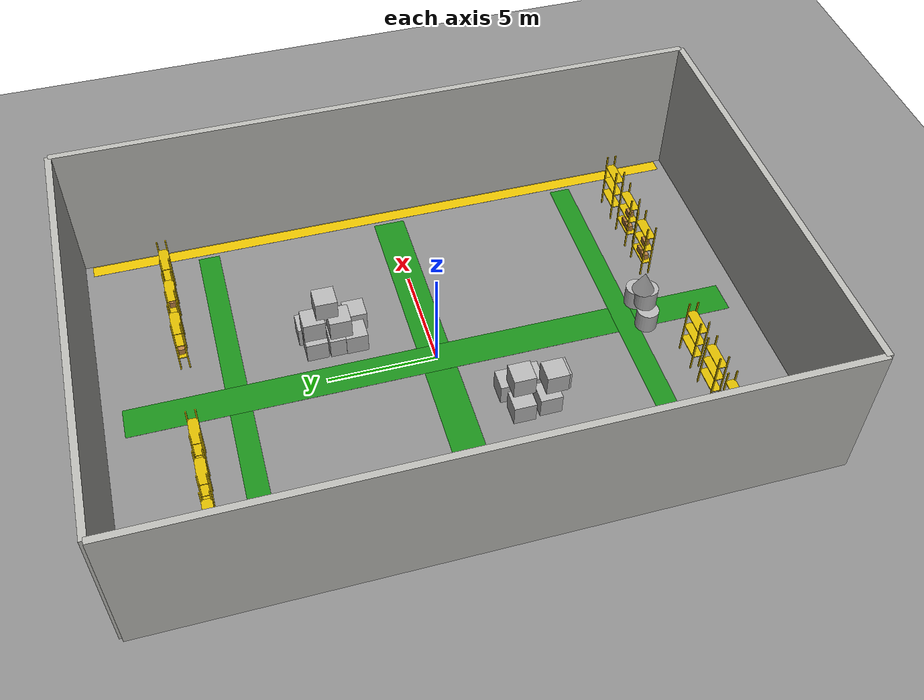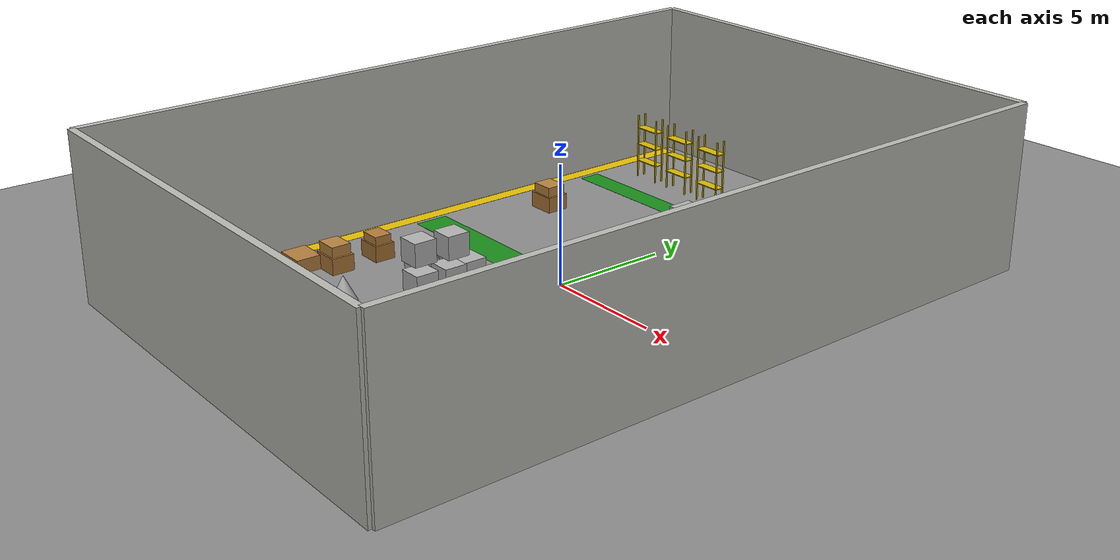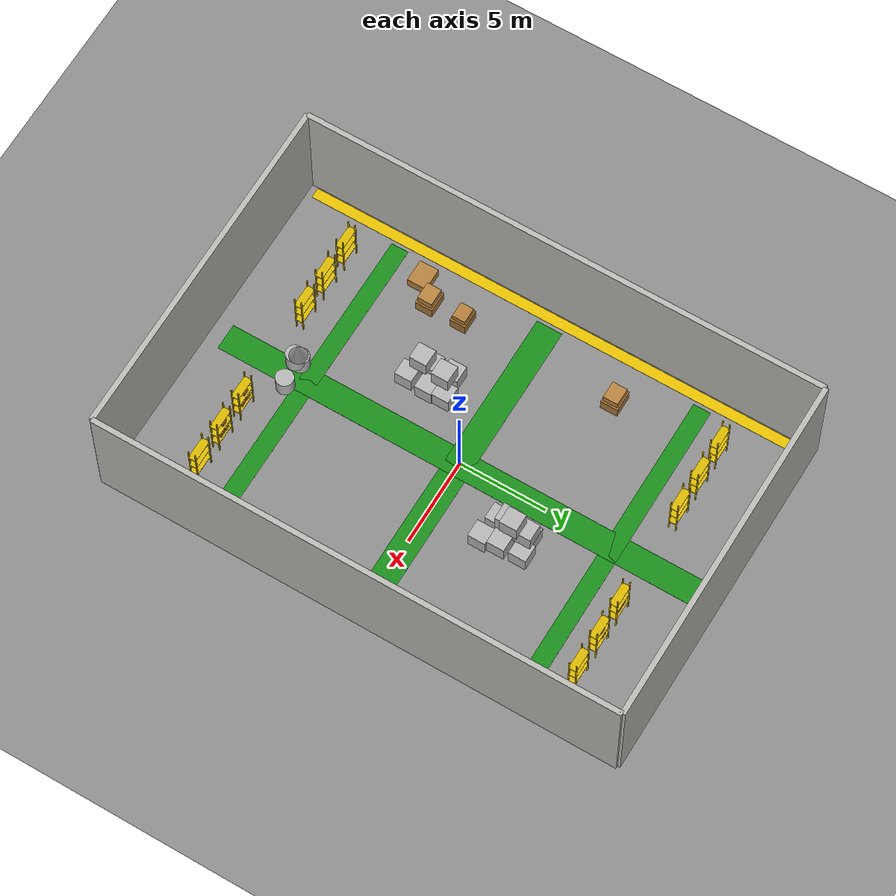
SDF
<sdf version="1.10">
 <world name="default">
  <physics name="1ms" type="ode">
   <max_step_size>0.001</max_step_size>
   <real_time_factor>1</real_time_factor>
   <real_time_update_rate>1000</real_time_update_rate>
  </physics>
  <plugin name="gz::sim::systems::Physics" filename="gz-sim-physics-system"/>
  <plugin name="gz::sim::systems::UserCommands" filename="gz-sim-user-commands-system"/>
  <plugin name="gz::sim::systems::SceneBroadcaster" filename="gz-sim-scene-broadcaster-system"/>
  <plugin name="gz::sim::systems::Sensors" filename="gz-sim-sensors-system">
   <render_engine>ogre2</render_engine>
  </plugin>
  <plugin name="gz::sim::systems::Contact" filename="gz-sim-contact-system"/>
  <gravity>0 0 -9.8000000000000007</gravity>
  <magnetic_field>5.5644999999999998e-06 2.2875799999999999e-05 -4.2388400000000002e-05</magnetic_field>
  <atmosphere type="adiabatic"/>
  <scene>
   <ambient>0.400000006 0.400000006 0.400000006 1</ambient>
   <background>0.699999988 0.699999988 0.699999988 1</background>
   <shadows>true</shadows>
  </scene>
  <model name="ground_plane">
   <static>true</static>
   <link name="link">
    <collision name="collision">
     <geometry><plane><normal>0 0 1</normal><size>40 30</size></plane></geometry>
     <surface><friction><ode><mu>0.0000000000000004</mu><mu2>0.0000000000000004</mu2></ode></friction></surface>
    </collision>
    <visual name="visual">
     <geometry><plane><normal>0 0 1</normal><size>20 30</size></plane></geometry>
     <material>
      <ambient>0.550000012 0.550000012 0.550000012 1</ambient>
      <diffuse>0.550000012 0.550000012 0.550000012 1</diffuse>
      <specular>0.100000001 0.100000001 0.100000001 1</specular>
     </material>
    </visual>
    <inertial>
     <mass>1</mass>
     <inertia><ixx>1</ixx><ixy>0</ixy><ixz>0</ixz><iyy>1</iyy><iyz>0</iyz><izz>1</izz></inertia>
    </inertial>
   </link>
  </model>
  <model name="wall_back">
   <static>true</static>
   <pose>10 0 3.5 0 0 0</pose>
   <link name="link">
    <collision name="c"><geometry><box><size>0.29999999999999999 30 7</size></box></geometry></collision>
    <visual name="v">
     <geometry><box><size>0.29999999999999999 30 7</size></box></geometry>
     <material>
      <ambient>0.720000029 0.720000029 0.699999988 1</ambient>
      <diffuse>0.720000029 0.720000029 0.699999988 1</diffuse>
     </material>
    </visual>
    <inertial>
     <mass>1</mass>
     <inertia><ixx>1</ixx><ixy>0</ixy><ixz>0</ixz><iyy>1</iyy><iyz>0</iyz><izz>1</izz></inertia>
    </inertial>
   </link>
  </model>
  <model name="wall_front">
   <static>true</static>
   <pose>-10 0 3.5 0 0 0</pose>
   <link name="link">
    <collision name="c"><geometry><box><size>0.29999999999999999 30 7</size></box></geometry></collision>
    <visual name="v">
     <geometry><box><size>0.29999999999999999 30 7</size></box></geometry>
     <material>
      <ambient>0.720000029 0.720000029 0.699999988 1</ambient>
      <diffuse>0.720000029 0.720000029 0.699999988 1</diffuse>
     </material>
    </visual>
    <inertial>
     <mass>1</mass>
     <inertia><ixx>1</ixx><ixy>0</ixy><ixz>0</ixz><iyy>1</iyy><iyz>0</iyz><izz>1</izz></inertia>
    </inertial>
   </link>
  </model>
  <model name="wall_left">
   <static>true</static>
   <pose>0 -15 3.5 0 0 0</pose>
   <link name="link">
    <collision name="c"><geometry><box><size>20 0.29999999999999999 7</size></box></geometry></collision>
    <visual name="v">
     <geometry><box><size>20 0.29999999999999999 7</size></box></geometry>
     <material>
      <ambient>0.720000029 0.720000029 0.699999988 1</ambient>
      <diffuse>0.720000029 0.720000029 0.699999988 1</diffuse>
     </material>
    </visual>
    <inertial>
     <mass>1</mass>
     <inertia><ixx>1</ixx><ixy>0</ixy><ixz>0</ixz><iyy>1</iyy><iyz>0</iyz><izz>1</izz></inertia>
    </inertial>
   </link>
  </model>
  <model name="wall_right">
   <static>true</static>
   <pose>0 15 3.5 0 0 0</pose>
   <link name="link">
    <collision name="c"><geometry><box><size>20 0.29999999999999999 7</size></box></geometry></collision>
    <visual name="v">
     <geometry><box><size>20 0.29999999999999999 7</size></box></geometry>
     <material>
      <ambient>0.720000029 0.720000029 0.699999988 1</ambient>
      <diffuse>0.720000029 0.720000029 0.699999988 1</diffuse>
     </material>
    </visual>
    <inertial>
     <mass>1</mass>
     <inertia><ixx>1</ixx><ixy>0</ixy><ixz>0</ixz><iyy>1</iyy><iyz>0</iyz><izz>1</izz></inertia>
    </inertial>
   </link>
  </model>
  <model name="lane_centre_x">
   <static>true</static>
   <pose>0 0 0.002 0 0 0</pose>
   <link name="link">
    <visual name="v">
     <geometry><box><size>18 1.5 0.0050000000000000001</size></box></geometry>
     <material>
      <ambient>0.100000001 0.550000012 0.100000001 1</ambient>
      <diffuse>0.100000001 0.550000012 0.100000001 1</diffuse>
     </material>
    </visual>
    <inertial>
     <mass>1</mass>
     <inertia><ixx>1</ixx><ixy>0</ixy><ixz>0</ixz><iyy>1</iyy><iyz>0</iyz><izz>1</izz></inertia>
    </inertial>
   </link>
  </model>
  <model name="lane_centre_y">
   <static>true</static>
   <pose>0 0 0.0020000000949949026 0 0 0</pose>
   <link name="link">
    <visual name="v">
     <geometry><box><size>1.5 28 0.0050000000000000001</size></box></geometry>
     <material>
      <ambient>0.100000001 0.550000012 0.100000001 1</ambient>
      <diffuse>0.100000001 0.550000012 0.100000001 1</diffuse>
     </material>
    </visual>
    <inertial>
     <mass>1</mass>
     <inertia><ixx>1</ixx><ixy>0</ixy><ixz>0</ixz><iyy>1</iyy><iyz>0</iyz><izz>1</izz></inertia>
    </inertial>
   </link>
  </model>
  <model name="lane_left">
   <static>true</static>
   <pose>0 -9 0.002 0 0 0</pose>
   <link name="link">
    <visual name="v">
     <geometry><box><size>18 1 0.0050000000000000001</size></box></geometry>
     <material>
      <ambient>0.100000001 0.550000012 0.100000001 1</ambient>
      <diffuse>0.100000001 0.550000012 0.100000001 1</diffuse>
     </material>
    </visual>
    <inertial>
     <mass>1</mass>
     <inertia><ixx>1</ixx><ixy>0</ixy><ixz>0</ixz><iyy>1</iyy><iyz>0</iyz><izz>1</izz></inertia>
    </inertial>
   </link>
  </model>
  <model name="lane_right">
   <static>true</static>
   <pose>0 9 0.002 0 0 0</pose>
   <link name="link">
    <visual name="v">
     <geometry><box><size>18 1 0.0050000000000000001</size></box></geometry>
     <material>
      <ambient>0.100000001 0.550000012 0.100000001 1</ambient>
      <diffuse>0.100000001 0.550000012 0.100000001 1</diffuse>
     </material>
    </visual>
    <inertial>
     <mass>1</mass>
     <inertia><ixx>1</ixx><ixy>0</ixy><ixz>0</ixz><iyy>1</iyy><iyz>0</iyz><izz>1</izz></inertia>
    </inertial>
   </link>
  </model>
  <model name="hazard_front">
   <static>true</static>
   <pose>-9.5 0 0.002 0 0 0</pose>
   <link name="link">
    <visual name="v">
     <geometry><box><size>0.59999999999999998 29 0.0050000000000000001</size></box></geometry>
     <material><ambient>0.899999976 0.75 0 1</ambient><diffuse>0.899999976 0.75 0 1</diffuse></material>
    </visual>
    <inertial>
     <mass>1</mass>
     <inertia><ixx>1</ixx><ixy>0</ixy><ixz>0</ixz><iyy>1</iyy><iyz>0</iyz><izz>1</izz></inertia>
    </inertial>
   </link>
  </model>
  <model name="hazard_back">
   <static>true</static>
   <pose>9.5 0 0.002 0 0 0</pose>
   <link name="link">
    <visual name="v">
     <geometry><box><size>0.59999999999999998 29 0.0050000000000000001</size></box></geometry>
     <material><ambient>0.899999976 0.75 0 1</ambient><diffuse>0.899999976 0.75 0 1</diffuse></material>
    </visual>
    <inertial>
     <mass>1</mass>
     <inertia><ixx>1</ixx><ixy>0</ixy><ixz>0</ixz><iyy>1</iyy><iyz>0</iyz><izz>1</izz></inertia>
    </inertial>
   </link>
  </model>
  <model name="shelf_A1">
   <static>true</static>
   <pose>3 -11 0 0 0 0</pose>
   <link name="link">
    <visual name="post_fl">
     <pose>-0.59999999999999998 -0.20000000000000001 1.5 0 0 0</pose>
     <geometry><box><size>0.059999999999999998 0.059999999999999998 3</size></box></geometry>
     <material>
      <ambient>0.850000024 0.720000029 0 1</ambient>
      <diffuse>0.850000024 0.720000029 0 1</diffuse>
     </material>
    </visual>
    <visual name="post_fr">
     <pose>0.59999999999999998 -0.20000000000000001 1.5 0 0 0</pose>
     <geometry><box><size>0.059999999999999998 0.059999999999999998 3</size></box></geometry>
     <material>
      <ambient>0.850000024 0.720000029 0 1</ambient>
      <diffuse>0.850000024 0.720000029 0 1</diffuse>
     </material>
    </visual>
    <visual name="post_bl">
     <pose>-0.59999999999999998 0.20000000000000001 1.5 0 0 0</pose>
     <geometry><box><size>0.059999999999999998 0.059999999999999998 3</size></box></geometry>
     <material>
      <ambient>0.850000024 0.720000029 0 1</ambient>
      <diffuse>0.850000024 0.720000029 0 1</diffuse>
     </material>
    </visual>
    <visual name="post_br">
     <pose>0.59999999999999998 0.20000000000000001 1.5 0 0 0</pose>
     <geometry><box><size>0.059999999999999998 0.059999999999999998 3</size></box></geometry>
     <material>
      <ambient>0.850000024 0.720000029 0 1</ambient>
      <diffuse>0.850000024 0.720000029 0 1</diffuse>
     </material>
    </visual>
    <visual name="shelf_l1">
     <pose>0 0 0.80000000000000004 0 0 0</pose>
     <geometry><box><size>1.3 0.45000000000000001 0.040000000000000001</size></box></geometry>
     <material>
      <ambient>0.850000024 0.720000029 0 1</ambient>
      <diffuse>0.850000024 0.720000029 0 1</diffuse>
     </material>
    </visual>
    <visual name="shelf_l2">
     <pose>0 0 1.6000000000000001 0 0 0</pose>
     <geometry><box><size>1.3 0.45000000000000001 0.040000000000000001</size></box></geometry>
     <material>
      <ambient>0.850000024 0.720000029 0 1</ambient>
      <diffuse>0.850000024 0.720000029 0 1</diffuse>
     </material>
    </visual>
    <visual name="shelf_l3">
     <pose>0 0 2.3999999999999999 0 0 0</pose>
     <geometry><box><size>1.3 0.45000000000000001 0.040000000000000001</size></box></geometry>
     <material>
      <ambient>0.850000024 0.720000029 0 1</ambient>
      <diffuse>0.850000024 0.720000029 0 1</diffuse>
     </material>
    </visual>
    <collision name="c">
     <geometry><box><size>1.3 0.5 3</size></box></geometry>
     <pose>0 0 1.5 0 0 0</pose>
    </collision>
    <inertial>
     <mass>1</mass>
     <inertia><ixx>1</ixx><ixy>0</ixy><ixz>0</ixz><iyy>1</iyy><iyz>0</iyz><izz>1</izz></inertia>
    </inertial>
   </link>
  </model>
  <model name="shelf_A2">
   <static>true</static>
   <pose>5 -11 0 0 0 0</pose>
   <link name="link">
    <visual name="post_fl">
     <pose>-0.59999999999999998 -0.20000000000000001 1.5 0 0 0</pose>
     <geometry><box><size>0.059999999999999998 0.059999999999999998 3</size></box></geometry>
     <material>
      <ambient>0.850000024 0.720000029 0 1</ambient>
      <diffuse>0.850000024 0.720000029 0 1</diffuse>
     </material>
    </visual>
    <visual name="post_fr">
     <pose>0.59999999999999998 -0.20000000000000001 1.5 0 0 0</pose>
     <geometry><box><size>0.059999999999999998 0.059999999999999998 3</size></box></geometry>
     <material>
      <ambient>0.850000024 0.720000029 0 1</ambient>
      <diffuse>0.850000024 0.720000029 0 1</diffuse>
     </material>
    </visual>
    <visual name="post_bl">
     <pose>-0.59999999999999998 0.20000000000000001 1.5 0 0 0</pose>
     <geometry><box><size>0.059999999999999998 0.059999999999999998 3</size></box></geometry>
     <material>
      <ambient>0.850000024 0.720000029 0 1</ambient>
      <diffuse>0.850000024 0.720000029 0 1</diffuse>
     </material>
    </visual>
    <visual name="post_br">
     <pose>0.59999999999999998 0.20000000000000001 1.5 0 0 0</pose>
     <geometry><box><size>0.059999999999999998 0.059999999999999998 3</size></box></geometry>
     <material>
      <ambient>0.850000024 0.720000029 0 1</ambient>
      <diffuse>0.850000024 0.720000029 0 1</diffuse>
     </material>
    </visual>
    <visual name="shelf_l1">
     <pose>0 0 0.80000000000000004 0 0 0</pose>
     <geometry><box><size>1.3 0.45000000000000001 0.040000000000000001</size></box></geometry>
     <material>
      <ambient>0.850000024 0.720000029 0 1</ambient>
      <diffuse>0.850000024 0.720000029 0 1</diffuse>
     </material>
    </visual>
    <visual name="shelf_l2">
     <pose>0 0 1.6000000000000001 0 0 0</pose>
     <geometry><box><size>1.3 0.45000000000000001 0.040000000000000001</size></box></geometry>
     <material>
      <ambient>0.850000024 0.720000029 0 1</ambient>
      <diffuse>0.850000024 0.720000029 0 1</diffuse>
     </material>
    </visual>
    <visual name="shelf_l3">
     <pose>0 0 2.3999999999999999 0 0 0</pose>
     <geometry><box><size>1.3 0.45000000000000001 0.040000000000000001</size></box></geometry>
     <material>
      <ambient>0.850000024 0.720000029 0 1</ambient>
      <diffuse>0.850000024 0.720000029 0 1</diffuse>
     </material>
    </visual>
    <collision name="c">
     <geometry><box><size>1.3 0.5 3</size></box></geometry>
     <pose>0 0 1.5 0 0 0</pose>
    </collision>
    <inertial>
     <mass>1</mass>
     <inertia><ixx>1</ixx><ixy>0</ixy><ixz>0</ixz><iyy>1</iyy><iyz>0</iyz><izz>1</izz></inertia>
    </inertial>
   </link>
  </model>
  <model name="shelf_A3">
   <static>true</static>
   <pose>7 -11 0 0 0 0</pose>
   <link name="link">
    <visual name="post_fl">
     <pose>-0.59999999999999998 -0.20000000000000001 1.5 0 0 0</pose>
     <geometry><box><size>0.059999999999999998 0.059999999999999998 3</size></box></geometry>
     <material>
      <ambient>0.850000024 0.720000029 0 1</ambient>
      <diffuse>0.850000024 0.720000029 0 1</diffuse>
     </material>
    </visual>
    <visual name="post_fr">
     <pose>0.59999999999999998 -0.20000000000000001 1.5 0 0 0</pose>
     <geometry><box><size>0.059999999999999998 0.059999999999999998 3</size></box></geometry>
     <material>
      <ambient>0.850000024 0.720000029 0 1</ambient>
      <diffuse>0.850000024 0.720000029 0 1</diffuse>
     </material>
    </visual>
    <visual name="post_bl">
     <pose>-0.59999999999999998 0.20000000000000001 1.5 0 0 0</pose>
     <geometry><box><size>0.059999999999999998 0.059999999999999998 3</size></box></geometry>
     <material>
      <ambient>0.850000024 0.720000029 0 1</ambient>
      <diffuse>0.850000024 0.720000029 0 1</diffuse>
     </material>
    </visual>
    <visual name="post_br">
     <pose>0.59999999999999998 0.20000000000000001 1.5 0 0 0</pose>
     <geometry><box><size>0.059999999999999998 0.059999999999999998 3</size></box></geometry>
     <material>
      <ambient>0.850000024 0.720000029 0 1</ambient>
      <diffuse>0.850000024 0.720000029 0 1</diffuse>
     </material>
    </visual>
    <visual name="shelf_l1">
     <pose>0 0 0.80000000000000004 0 0 0</pose>
     <geometry><box><size>1.3 0.45000000000000001 0.040000000000000001</size></box></geometry>
     <material>
      <ambient>0.850000024 0.720000029 0 1</ambient>
      <diffuse>0.850000024 0.720000029 0 1</diffuse>
     </material>
    </visual>
    <visual name="shelf_l2">
     <pose>0 0 1.6000000000000001 0 0 0</pose>
     <geometry><box><size>1.3 0.45000000000000001 0.040000000000000001</size></box></geometry>
     <material>
      <ambient>0.850000024 0.720000029 0 1</ambient>
      <diffuse>0.850000024 0.720000029 0 1</diffuse>
     </material>
    </visual>
    <visual name="shelf_l3">
     <pose>0 0 2.3999999999999999 0 0 0</pose>
     <geometry><box><size>1.3 0.45000000000000001 0.040000000000000001</size></box></geometry>
     <material>
      <ambient>0.850000024 0.720000029 0 1</ambient>
      <diffuse>0.850000024 0.720000029 0 1</diffuse>
     </material>
    </visual>
    <collision name="c">
     <geometry><box><size>1.3 0.5 3</size></box></geometry>
     <pose>0 0 1.5 0 0 0</pose>
    </collision>
    <inertial>
     <mass>1</mass>
     <inertia><ixx>1</ixx><ixy>0</ixy><ixz>0</ixz><iyy>1</iyy><iyz>0</iyz><izz>1</izz></inertia>
    </inertial>
   </link>
  </model>
  <model name="shelf_B1">
   <static>true</static>
   <pose>3 11 0 0 0 0</pose>
   <link name="link">
    <visual name="post_fl">
     <pose>-0.59999999999999998 -0.20000000000000001 1.5 0 0 0</pose>
     <geometry><box><size>0.059999999999999998 0.059999999999999998 3</size></box></geometry>
     <material>
      <ambient>0.850000024 0.720000029 0 1</ambient>
      <diffuse>0.850000024 0.720000029 0 1</diffuse>
     </material>
    </visual>
    <visual name="post_fr">
     <pose>0.59999999999999998 -0.20000000000000001 1.5 0 0 0</pose>
     <geometry><box><size>0.059999999999999998 0.059999999999999998 3</size></box></geometry>
     <material>
      <ambient>0.850000024 0.720000029 0 1</ambient>
      <diffuse>0.850000024 0.720000029 0 1</diffuse>
     </material>
    </visual>
    <visual name="post_bl">
     <pose>-0.59999999999999998 0.20000000000000001 1.5 0 0 0</pose>
     <geometry><box><size>0.059999999999999998 0.059999999999999998 3</size></box></geometry>
     <material>
      <ambient>0.850000024 0.720000029 0 1</ambient>
      <diffuse>0.850000024 0.720000029 0 1</diffuse>
     </material>
    </visual>
    <visual name="post_br">
     <pose>0.59999999999999998 0.20000000000000001 1.5 0 0 0</pose>
     <geometry><box><size>0.059999999999999998 0.059999999999999998 3</size></box></geometry>
     <material>
      <ambient>0.850000024 0.720000029 0 1</ambient>
      <diffuse>0.850000024 0.720000029 0 1</diffuse>
     </material>
    </visual>
    <visual name="shelf_l1">
     <pose>0 0 0.80000000000000004 0 0 0</pose>
     <geometry><box><size>1.3 0.45000000000000001 0.040000000000000001</size></box></geometry>
     <material>
      <ambient>0.850000024 0.720000029 0 1</ambient>
      <diffuse>0.850000024 0.720000029 0 1</diffuse>
     </material>
    </visual>
    <visual name="shelf_l2">
     <pose>0 0 1.6000000000000001 0 0 0</pose>
     <geometry><box><size>1.3 0.45000000000000001 0.040000000000000001</size></box></geometry>
     <material>
      <ambient>0.850000024 0.720000029 0 1</ambient>
      <diffuse>0.850000024 0.720000029 0 1</diffuse>
     </material>
    </visual>
    <visual name="shelf_l3">
     <pose>0 0 2.3999999999999999 0 0 0</pose>
     <geometry><box><size>1.3 0.45000000000000001 0.040000000000000001</size></box></geometry>
     <material>
      <ambient>0.850000024 0.720000029 0 1</ambient>
      <diffuse>0.850000024 0.720000029 0 1</diffuse>
     </material>
    </visual>
    <collision name="c">
     <geometry><box><size>1.3 0.5 3</size></box></geometry>
     <pose>0 0 1.5 0 0 0</pose>
    </collision>
    <inertial>
     <mass>1</mass>
     <inertia><ixx>1</ixx><ixy>0</ixy><ixz>0</ixz><iyy>1</iyy><iyz>0</iyz><izz>1</izz></inertia>
    </inertial>
   </link>
  </model>
  <model name="shelf_B2">
   <static>true</static>
   <pose>5 11 0 0 0 0</pose>
   <link name="link">
    <visual name="post_fl">
     <pose>-0.59999999999999998 -0.20000000000000001 1.5 0 0 0</pose>
     <geometry><box><size>0.059999999999999998 0.059999999999999998 3</size></box></geometry>
     <material>
      <ambient>0.850000024 0.720000029 0 1</ambient>
      <diffuse>0.850000024 0.720000029 0 1</diffuse>
     </material>
    </visual>
    <visual name="post_fr">
     <pose>0.59999999999999998 -0.20000000000000001 1.5 0 0 0</pose>
     <geometry><box><size>0.059999999999999998 0.059999999999999998 3</size></box></geometry>
     <material>
      <ambient>0.850000024 0.720000029 0 1</ambient>
      <diffuse>0.850000024 0.720000029 0 1</diffuse>
     </material>
    </visual>
    <visual name="post_bl">
     <pose>-0.59999999999999998 0.20000000000000001 1.5 0 0 0</pose>
     <geometry><box><size>0.059999999999999998 0.059999999999999998 3</size></box></geometry>
     <material>
      <ambient>0.850000024 0.720000029 0 1</ambient>
      <diffuse>0.850000024 0.720000029 0 1</diffuse>
     </material>
    </visual>
    <visual name="post_br">
     <pose>0.59999999999999998 0.20000000000000001 1.5 0 0 0</pose>
     <geometry><box><size>0.059999999999999998 0.059999999999999998 3</size></box></geometry>
     <material>
      <ambient>0.850000024 0.720000029 0 1</ambient>
      <diffuse>0.850000024 0.720000029 0 1</diffuse>
     </material>
    </visual>
    <visual name="shelf_l1">
     <pose>0 0 0.80000000000000004 0 0 0</pose>
     <geometry><box><size>1.3 0.45000000000000001 0.040000000000000001</size></box></geometry>
     <material>
      <ambient>0.850000024 0.720000029 0 1</ambient>
      <diffuse>0.850000024 0.720000029 0 1</diffuse>
     </material>
    </visual>
    <visual name="shelf_l2">
     <pose>0 0 1.6000000000000001 0 0 0</pose>
     <geometry><box><size>1.3 0.45000000000000001 0.040000000000000001</size></box></geometry>
     <material>
      <ambient>0.850000024 0.720000029 0 1</ambient>
      <diffuse>0.850000024 0.720000029 0 1</diffuse>
     </material>
    </visual>
    <visual name="shelf_l3">
     <pose>0 0 2.3999999999999999 0 0 0</pose>
     <geometry><box><size>1.3 0.45000000000000001 0.040000000000000001</size></box></geometry>
     <material>
      <ambient>0.850000024 0.720000029 0 1</ambient>
      <diffuse>0.850000024 0.720000029 0 1</diffuse>
     </material>
    </visual>
    <collision name="c">
     <geometry><box><size>1.3 0.5 3</size></box></geometry>
     <pose>0 0 1.5 0 0 0</pose>
    </collision>
    <inertial>
     <mass>1</mass>
     <inertia><ixx>1</ixx><ixy>0</ixy><ixz>0</ixz><iyy>1</iyy><iyz>0</iyz><izz>1</izz></inertia>
    </inertial>
   </link>
  </model>
  <model name="shelf_B3">
   <static>true</static>
   <pose>7 11 0 0 0 0</pose>
   <link name="link">
    <visual name="post_fl">
     <pose>-0.59999999999999998 -0.20000000000000001 1.5 0 0 0</pose>
     <geometry><box><size>0.059999999999999998 0.059999999999999998 3</size></box></geometry>
     <material>
      <ambient>0.850000024 0.720000029 0 1</ambient>
      <diffuse>0.850000024 0.720000029 0 1</diffuse>
     </material>
    </visual>
    <visual name="post_fr">
     <pose>0.59999999999999998 -0.20000000000000001 1.5 0 0 0</pose>
     <geometry><box><size>0.059999999999999998 0.059999999999999998 3</size></box></geometry>
     <material>
      <ambient>0.850000024 0.720000029 0 1</ambient>
      <diffuse>0.850000024 0.720000029 0 1</diffuse>
     </material>
    </visual>
    <visual name="post_bl">
     <pose>-0.59999999999999998 0.20000000000000001 1.5 0 0 0</pose>
     <geometry><box><size>0.059999999999999998 0.059999999999999998 3</size></box></geometry>
     <material>
      <ambient>0.850000024 0.720000029 0 1</ambient>
      <diffuse>0.850000024 0.720000029 0 1</diffuse>
     </material>
    </visual>
    <visual name="post_br">
     <pose>0.59999999999999998 0.20000000000000001 1.5 0 0 0</pose>
     <geometry><box><size>0.059999999999999998 0.059999999999999998 3</size></box></geometry>
     <material>
      <ambient>0.850000024 0.720000029 0 1</ambient>
      <diffuse>0.850000024 0.720000029 0 1</diffuse>
     </material>
    </visual>
    <visual name="shelf_l1">
     <pose>0 0 0.80000000000000004 0 0 0</pose>
     <geometry><box><size>1.3 0.45000000000000001 0.040000000000000001</size></box></geometry>
     <material>
      <ambient>0.850000024 0.720000029 0 1</ambient>
      <diffuse>0.850000024 0.720000029 0 1</diffuse>
     </material>
    </visual>
    <visual name="shelf_l2">
     <pose>0 0 1.6000000000000001 0 0 0</pose>
     <geometry><box><size>1.3 0.45000000000000001 0.040000000000000001</size></box></geometry>
     <material>
      <ambient>0.850000024 0.720000029 0 1</ambient>
      <diffuse>0.850000024 0.720000029 0 1</diffuse>
     </material>
    </visual>
    <visual name="shelf_l3">
     <pose>0 0 2.3999999999999999 0 0 0</pose>
     <geometry><box><size>1.3 0.45000000000000001 0.040000000000000001</size></box></geometry>
     <material>
      <ambient>0.850000024 0.720000029 0 1</ambient>
      <diffuse>0.850000024 0.720000029 0 1</diffuse>
     </material>
    </visual>
    <collision name="c">
     <geometry><box><size>1.3 0.5 3</size></box></geometry>
     <pose>0 0 1.5 0 0 0</pose>
    </collision>
    <inertial>
     <mass>1</mass>
     <inertia><ixx>1</ixx><ixy>0</ixy><ixz>0</ixz><iyy>1</iyy><iyz>0</iyz><izz>1</izz></inertia>
    </inertial>
   </link>
  </model>
  <model name="shelf_C1">
   <static>true</static>
   <pose>-3 -11 0 0 0 0</pose>
   <link name="link">
    <visual name="post_fl">
     <pose>-0.59999999999999998 -0.20000000000000001 1.5 0 0 0</pose>
     <geometry><box><size>0.059999999999999998 0.059999999999999998 3</size></box></geometry>
     <material>
      <ambient>0.850000024 0.720000029 0 1</ambient>
      <diffuse>0.850000024 0.720000029 0 1</diffuse>
     </material>
    </visual>
    <visual name="post_fr">
     <pose>0.59999999999999998 -0.20000000000000001 1.5 0 0 0</pose>
     <geometry><box><size>0.059999999999999998 0.059999999999999998 3</size></box></geometry>
     <material>
      <ambient>0.850000024 0.720000029 0 1</ambient>
      <diffuse>0.850000024 0.720000029 0 1</diffuse>
     </material>
    </visual>
    <visual name="post_bl">
     <pose>-0.59999999999999998 0.20000000000000001 1.5 0 0 0</pose>
     <geometry><box><size>0.059999999999999998 0.059999999999999998 3</size></box></geometry>
     <material>
      <ambient>0.850000024 0.720000029 0 1</ambient>
      <diffuse>0.850000024 0.720000029 0 1</diffuse>
     </material>
    </visual>
    <visual name="post_br">
     <pose>0.59999999999999998 0.20000000000000001 1.5 0 0 0</pose>
     <geometry><box><size>0.059999999999999998 0.059999999999999998 3</size></box></geometry>
     <material>
      <ambient>0.850000024 0.720000029 0 1</ambient>
      <diffuse>0.850000024 0.720000029 0 1</diffuse>
     </material>
    </visual>
    <visual name="shelf_l1">
     <pose>0 0 0.80000000000000004 0 0 0</pose>
     <geometry><box><size>1.3 0.45000000000000001 0.040000000000000001</size></box></geometry>
     <material>
      <ambient>0.850000024 0.720000029 0 1</ambient>
      <diffuse>0.850000024 0.720000029 0 1</diffuse>
     </material>
    </visual>
    <visual name="shelf_l2">
     <pose>0 0 1.6000000000000001 0 0 0</pose>
     <geometry><box><size>1.3 0.45000000000000001 0.040000000000000001</size></box></geometry>
     <material>
      <ambient>0.850000024 0.720000029 0 1</ambient>
      <diffuse>0.850000024 0.720000029 0 1</diffuse>
     </material>
    </visual>
    <visual name="shelf_l3">
     <pose>0 0 2.3999999999999999 0 0 0</pose>
     <geometry><box><size>1.3 0.45000000000000001 0.040000000000000001</size></box></geometry>
     <material>
      <ambient>0.850000024 0.720000029 0 1</ambient>
      <diffuse>0.850000024 0.720000029 0 1</diffuse>
     </material>
    </visual>
    <collision name="c">
     <geometry><box><size>1.3 0.5 3</size></box></geometry>
     <pose>0 0 1.5 0 0 0</pose>
    </collision>
    <inertial>
     <mass>1</mass>
     <inertia><ixx>1</ixx><ixy>0</ixy><ixz>0</ixz><iyy>1</iyy><iyz>0</iyz><izz>1</izz></inertia>
    </inertial>
   </link>
  </model>
  <model name="shelf_C2">
   <static>true</static>
   <pose>-5 -11 0 0 0 0</pose>
   <link name="link">
    <visual name="post_fl">
     <pose>-0.59999999999999998 -0.20000000000000001 1.5 0 0 0</pose>
     <geometry><box><size>0.059999999999999998 0.059999999999999998 3</size></box></geometry>
     <material>
      <ambient>0.850000024 0.720000029 0 1</ambient>
      <diffuse>0.850000024 0.720000029 0 1</diffuse>
     </material>
    </visual>
    <visual name="post_fr">
     <pose>0.59999999999999998 -0.20000000000000001 1.5 0 0 0</pose>
     <geometry><box><size>0.059999999999999998 0.059999999999999998 3</size></box></geometry>
     <material>
      <ambient>0.850000024 0.720000029 0 1</ambient>
      <diffuse>0.850000024 0.720000029 0 1</diffuse>
     </material>
    </visual>
    <visual name="post_bl">
     <pose>-0.59999999999999998 0.20000000000000001 1.5 0 0 0</pose>
     <geometry><box><size>0.059999999999999998 0.059999999999999998 3</size></box></geometry>
     <material>
      <ambient>0.850000024 0.720000029 0 1</ambient>
      <diffuse>0.850000024 0.720000029 0 1</diffuse>
     </material>
    </visual>
    <visual name="post_br">
     <pose>0.59999999999999998 0.20000000000000001 1.5 0 0 0</pose>
     <geometry><box><size>0.059999999999999998 0.059999999999999998 3</size></box></geometry>
     <material>
      <ambient>0.850000024 0.720000029 0 1</ambient>
      <diffuse>0.850000024 0.720000029 0 1</diffuse>
     </material>
    </visual>
    <visual name="shelf_l1">
     <pose>0 0 0.80000000000000004 0 0 0</pose>
     <geometry><box><size>1.3 0.45000000000000001 0.040000000000000001</size></box></geometry>
     <material>
      <ambient>0.850000024 0.720000029 0 1</ambient>
      <diffuse>0.850000024 0.720000029 0 1</diffuse>
     </material>
    </visual>
    <visual name="shelf_l2">
     <pose>0 0 1.6000000000000001 0 0 0</pose>
     <geometry><box><size>1.3 0.45000000000000001 0.040000000000000001</size></box></geometry>
     <material>
      <ambient>0.850000024 0.720000029 0 1</ambient>
      <diffuse>0.850000024 0.720000029 0 1</diffuse>
     </material>
    </visual>
    <visual name="shelf_l3">
     <pose>0 0 2.3999999999999999 0 0 0</pose>
     <geometry><box><size>1.3 0.45000000000000001 0.040000000000000001</size></box></geometry>
     <material>
      <ambient>0.850000024 0.720000029 0 1</ambient>
      <diffuse>0.850000024 0.720000029 0 1</diffuse>
     </material>
    </visual>
    <collision name="c">
     <geometry><box><size>1.3 0.5 3</size></box></geometry>
     <pose>0 0 1.5 0 0 0</pose>
    </collision>
    <inertial>
     <mass>1</mass>
     <inertia><ixx>1</ixx><ixy>0</ixy><ixz>0</ixz><iyy>1</iyy><iyz>0</iyz><izz>1</izz></inertia>
    </inertial>
   </link>
  </model>
  <model name="shelf_C3">
   <static>true</static>
   <pose>-7 -11 0 0 0 0</pose>
   <link name="link">
    <visual name="post_fl">
     <pose>-0.59999999999999998 -0.20000000000000001 1.5 0 0 0</pose>
     <geometry><box><size>0.059999999999999998 0.059999999999999998 3</size></box></geometry>
     <material>
      <ambient>0.850000024 0.720000029 0 1</ambient>
      <diffuse>0.850000024 0.720000029 0 1</diffuse>
     </material>
    </visual>
    <visual name="post_fr">
     <pose>0.59999999999999998 -0.20000000000000001 1.5 0 0 0</pose>
     <geometry><box><size>0.059999999999999998 0.059999999999999998 3</size></box></geometry>
     <material>
      <ambient>0.850000024 0.720000029 0 1</ambient>
      <diffuse>0.850000024 0.720000029 0 1</diffuse>
     </material>
    </visual>
    <visual name="post_bl">
     <pose>-0.59999999999999998 0.20000000000000001 1.5 0 0 0</pose>
     <geometry><box><size>0.059999999999999998 0.059999999999999998 3</size></box></geometry>
     <material>
      <ambient>0.850000024 0.720000029 0 1</ambient>
      <diffuse>0.850000024 0.720000029 0 1</diffuse>
     </material>
    </visual>
    <visual name="post_br">
     <pose>0.59999999999999998 0.20000000000000001 1.5 0 0 0</pose>
     <geometry><box><size>0.059999999999999998 0.059999999999999998 3</size></box></geometry>
     <material>
      <ambient>0.850000024 0.720000029 0 1</ambient>
      <diffuse>0.850000024 0.720000029 0 1</diffuse>
     </material>
    </visual>
    <visual name="shelf_l1">
     <pose>0 0 0.80000000000000004 0 0 0</pose>
     <geometry><box><size>1.3 0.45000000000000001 0.040000000000000001</size></box></geometry>
     <material>
      <ambient>0.850000024 0.720000029 0 1</ambient>
      <diffuse>0.850000024 0.720000029 0 1</diffuse>
     </material>
    </visual>
    <visual name="shelf_l2">
     <pose>0 0 1.6000000000000001 0 0 0</pose>
     <geometry><box><size>1.3 0.45000000000000001 0.040000000000000001</size></box></geometry>
     <material>
      <ambient>0.850000024 0.720000029 0 1</ambient>
      <diffuse>0.850000024 0.720000029 0 1</diffuse>
     </material>
    </visual>
    <visual name="shelf_l3">
     <pose>0 0 2.3999999999999999 0 0 0</pose>
     <geometry><box><size>1.3 0.45000000000000001 0.040000000000000001</size></box></geometry>
     <material>
      <ambient>0.850000024 0.720000029 0 1</ambient>
      <diffuse>0.850000024 0.720000029 0 1</diffuse>
     </material>
    </visual>
    <collision name="c">
     <geometry><box><size>1.3 0.5 3</size></box></geometry>
     <pose>0 0 1.5 0 0 0</pose>
    </collision>
    <inertial>
     <mass>1</mass>
     <inertia><ixx>1</ixx><ixy>0</ixy><ixz>0</ixz><iyy>1</iyy><iyz>0</iyz><izz>1</izz></inertia>
    </inertial>
   </link>
  </model>
  <model name="shelf_D1">
   <static>true</static>
   <pose>-3 11 0 0 0 0</pose>
   <link name="link">
    <visual name="post_fl">
     <pose>-0.59999999999999998 -0.20000000000000001 1.5 0 0 0</pose>
     <geometry><box><size>0.059999999999999998 0.059999999999999998 3</size></box></geometry>
     <material>
      <ambient>0.850000024 0.720000029 0 1</ambient>
      <diffuse>0.850000024 0.720000029 0 1</diffuse>
     </material>
    </visual>
    <visual name="post_fr">
     <pose>0.59999999999999998 -0.20000000000000001 1.5 0 0 0</pose>
     <geometry><box><size>0.059999999999999998 0.059999999999999998 3</size></box></geometry>
     <material>
      <ambient>0.850000024 0.720000029 0 1</ambient>
      <diffuse>0.850000024 0.720000029 0 1</diffuse>
     </material>
    </visual>
    <visual name="post_bl">
     <pose>-0.59999999999999998 0.20000000000000001 1.5 0 0 0</pose>
     <geometry><box><size>0.059999999999999998 0.059999999999999998 3</size></box></geometry>
     <material>
      <ambient>0.850000024 0.720000029 0 1</ambient>
      <diffuse>0.850000024 0.720000029 0 1</diffuse>
     </material>
    </visual>
    <visual name="post_br">
     <pose>0.59999999999999998 0.20000000000000001 1.5 0 0 0</pose>
     <geometry><box><size>0.059999999999999998 0.059999999999999998 3</size></box></geometry>
     <material>
      <ambient>0.850000024 0.720000029 0 1</ambient>
      <diffuse>0.850000024 0.720000029 0 1</diffuse>
     </material>
    </visual>
    <visual name="shelf_l1">
     <pose>0 0 0.80000000000000004 0 0 0</pose>
     <geometry><box><size>1.3 0.45000000000000001 0.040000000000000001</size></box></geometry>
     <material>
      <ambient>0.850000024 0.720000029 0 1</ambient>
      <diffuse>0.850000024 0.720000029 0 1</diffuse>
     </material>
    </visual>
    <visual name="shelf_l2">
     <pose>0 0 1.6000000000000001 0 0 0</pose>
     <geometry><box><size>1.3 0.45000000000000001 0.040000000000000001</size></box></geometry>
     <material>
      <ambient>0.850000024 0.720000029 0 1</ambient>
      <diffuse>0.850000024 0.720000029 0 1</diffuse>
     </material>
    </visual>
    <visual name="shelf_l3">
     <pose>0 0 2.3999999999999999 0 0 0</pose>
     <geometry><box><size>1.3 0.45000000000000001 0.040000000000000001</size></box></geometry>
     <material>
      <ambient>0.850000024 0.720000029 0 1</ambient>
      <diffuse>0.850000024 0.720000029 0 1</diffuse>
     </material>
    </visual>
    <collision name="c">
     <geometry><box><size>1.3 0.5 3</size></box></geometry>
     <pose>0 0 1.5 0 0 0</pose>
    </collision>
    <inertial>
     <mass>1</mass>
     <inertia><ixx>1</ixx><ixy>0</ixy><ixz>0</ixz><iyy>1</iyy><iyz>0</iyz><izz>1</izz></inertia>
    </inertial>
   </link>
  </model>
  <model name="shelf_D2">
   <static>true</static>
   <pose>-5 11 0 0 0 0</pose>
   <link name="link">
    <visual name="post_fl">
     <pose>-0.59999999999999998 -0.20000000000000001 1.5 0 0 0</pose>
     <geometry><box><size>0.059999999999999998 0.059999999999999998 3</size></box></geometry>
     <material>
      <ambient>0.850000024 0.720000029 0 1</ambient>
      <diffuse>0.850000024 0.720000029 0 1</diffuse>
     </material>
    </visual>
    <visual name="post_fr">
     <pose>0.59999999999999998 -0.20000000000000001 1.5 0 0 0</pose>
     <geometry><box><size>0.059999999999999998 0.059999999999999998 3</size></box></geometry>
     <material>
      <ambient>0.850000024 0.720000029 0 1</ambient>
      <diffuse>0.850000024 0.720000029 0 1</diffuse>
     </material>
    </visual>
    <visual name="post_bl">
     <pose>-0.59999999999999998 0.20000000000000001 1.5 0 0 0</pose>
     <geometry><box><size>0.059999999999999998 0.059999999999999998 3</size></box></geometry>
     <material>
      <ambient>0.850000024 0.720000029 0 1</ambient>
      <diffuse>0.850000024 0.720000029 0 1</diffuse>
     </material>
    </visual>
    <visual name="post_br">
     <pose>0.59999999999999998 0.20000000000000001 1.5 0 0 0</pose>
     <geometry><box><size>0.059999999999999998 0.059999999999999998 3</size></box></geometry>
     <material>
      <ambient>0.850000024 0.720000029 0 1</ambient>
      <diffuse>0.850000024 0.720000029 0 1</diffuse>
     </material>
    </visual>
    <visual name="shelf_l1">
     <pose>0 0 0.80000000000000004 0 0 0</pose>
     <geometry><box><size>1.3 0.45000000000000001 0.040000000000000001</size></box></geometry>
     <material>
      <ambient>0.850000024 0.720000029 0 1</ambient>
      <diffuse>0.850000024 0.720000029 0 1</diffuse>
     </material>
    </visual>
    <visual name="shelf_l2">
     <pose>0 0 1.6000000000000001 0 0 0</pose>
     <geometry><box><size>1.3 0.45000000000000001 0.040000000000000001</size></box></geometry>
     <material>
      <ambient>0.850000024 0.720000029 0 1</ambient>
      <diffuse>0.850000024 0.720000029 0 1</diffuse>
     </material>
    </visual>
    <visual name="shelf_l3">
     <pose>0 0 2.3999999999999999 0 0 0</pose>
     <geometry><box><size>1.3 0.45000000000000001 0.040000000000000001</size></box></geometry>
     <material>
      <ambient>0.850000024 0.720000029 0 1</ambient>
      <diffuse>0.850000024 0.720000029 0 1</diffuse>
     </material>
    </visual>
    <collision name="c">
     <geometry><box><size>1.3 0.5 3</size></box></geometry>
     <pose>0 0 1.5 0 0 0</pose>
    </collision>
    <inertial>
     <mass>1</mass>
     <inertia><ixx>1</ixx><ixy>0</ixy><ixz>0</ixz><iyy>1</iyy><iyz>0</iyz><izz>1</izz></inertia>
    </inertial>
   </link>
  </model>
  <model name="shelf_D3">
   <static>true</static>
   <pose>-7 11 0 0 0 0</pose>
   <link name="link">
    <visual name="post_fl">
     <pose>-0.59999999999999998 -0.20000000000000001 1.5 0 0 0</pose>
     <geometry><box><size>0.059999999999999998 0.059999999999999998 3</size></box></geometry>
     <material>
      <ambient>0.850000024 0.720000029 0 1</ambient>
      <diffuse>0.850000024 0.720000029 0 1</diffuse>
     </material>
    </visual>
    <visual name="post_fr">
     <pose>0.59999999999999998 -0.20000000000000001 1.5 0 0 0</pose>
     <geometry><box><size>0.059999999999999998 0.059999999999999998 3</size></box></geometry>
     <material>
      <ambient>0.850000024 0.720000029 0 1</ambient>
      <diffuse>0.850000024 0.720000029 0 1</diffuse>
     </material>
    </visual>
    <visual name="post_bl">
     <pose>-0.59999999999999998 0.20000000000000001 1.5 0 0 0</pose>
     <geometry><box><size>0.059999999999999998 0.059999999999999998 3</size></box></geometry>
     <material>
      <ambient>0.850000024 0.720000029 0 1</ambient>
      <diffuse>0.850000024 0.720000029 0 1</diffuse>
     </material>
    </visual>
    <visual name="post_br">
     <pose>0.59999999999999998 0.20000000000000001 1.5 0 0 0</pose>
     <geometry><box><size>0.059999999999999998 0.059999999999999998 3</size></box></geometry>
     <material>
      <ambient>0.850000024 0.720000029 0 1</ambient>
      <diffuse>0.850000024 0.720000029 0 1</diffuse>
     </material>
    </visual>
    <visual name="shelf_l1">
     <pose>0 0 0.80000000000000004 0 0 0</pose>
     <geometry><box><size>1.3 0.45000000000000001 0.040000000000000001</size></box></geometry>
     <material>
      <ambient>0.850000024 0.720000029 0 1</ambient>
      <diffuse>0.850000024 0.720000029 0 1</diffuse>
     </material>
    </visual>
    <visual name="shelf_l2">
     <pose>0 0 1.6000000000000001 0 0 0</pose>
     <geometry><box><size>1.3 0.45000000000000001 0.040000000000000001</size></box></geometry>
     <material>
      <ambient>0.850000024 0.720000029 0 1</ambient>
      <diffuse>0.850000024 0.720000029 0 1</diffuse>
     </material>
    </visual>
    <visual name="shelf_l3">
     <pose>0 0 2.3999999999999999 0 0 0</pose>
     <geometry><box><size>1.3 0.45000000000000001 0.040000000000000001</size></box></geometry>
     <material>
      <ambient>0.850000024 0.720000029 0 1</ambient>
      <diffuse>0.850000024 0.720000029 0 1</diffuse>
     </material>
    </visual>
    <collision name="c">
     <geometry><box><size>1.3 0.5 3</size></box></geometry>
     <pose>0 0 1.5 0 0 0</pose>
    </collision>
    <inertial>
     <mass>1</mass>
     <inertia><ixx>1</ixx><ixy>0</ixy><ixz>0</ixz><iyy>1</iyy><iyz>0</iyz><izz>1</izz></inertia>
    </inertial>
   </link>
  </model>
  <model name="box_A1_l1_a">
   <static>true</static>
   <pose>2.7000000000000002 -11 0.96999999999999997 0 0 0</pose>
   <link name="link">
    <visual name="v">
     <geometry><box><size>0.32000000000000001 0.28000000000000003 0.29999999999999999</size></box></geometry>
     <material><ambient>0.720000029 0.5 0.25 1</ambient><diffuse>0.720000029 0.5 0.25 1</diffuse></material>
    </visual>
    <collision name="c">
     <geometry><box><size>0.32000000000000001 0.28000000000000003 0.29999999999999999</size></box></geometry>
    </collision>
    <inertial>
     <mass>1</mass>
     <inertia><ixx>1</ixx><ixy>0</ixy><ixz>0</ixz><iyy>1</iyy><iyz>0</iyz><izz>1</izz></inertia>
    </inertial>
   </link>
  </model>
  <model name="box_A1_l1_b">
   <static>true</static>
   <pose>3.1000000000000001 -11 0.96999999999999997 0 0 0</pose>
   <link name="link">
    <visual name="v">
     <geometry><box><size>0.32000000000000001 0.28000000000000003 0.29999999999999999</size></box></geometry>
     <material>
      <ambient>0.680000007 0.479999989 0.219999999 1</ambient>
      <diffuse>0.680000007 0.479999989 0.219999999 1</diffuse>
     </material>
    </visual>
    <collision name="c">
     <geometry><box><size>0.32000000000000001 0.28000000000000003 0.29999999999999999</size></box></geometry>
    </collision>
    <inertial>
     <mass>1</mass>
     <inertia><ixx>1</ixx><ixy>0</ixy><ixz>0</ixz><iyy>1</iyy><iyz>0</iyz><izz>1</izz></inertia>
    </inertial>
   </link>
  </model>
  <model name="box_A1_l2_a">
   <static>true</static>
   <pose>2.8500000000000001 -11 1.77 0 0 0</pose>
   <link name="link">
    <visual name="v">
     <geometry><box><size>0.32000000000000001 0.28000000000000003 0.29999999999999999</size></box></geometry>
     <material>
      <ambient>0.699999988 0.49000001 0.230000004 1</ambient>
      <diffuse>0.699999988 0.49000001 0.230000004 1</diffuse>
     </material>
    </visual>
    <collision name="c">
     <geometry><box><size>0.32000000000000001 0.28000000000000003 0.29999999999999999</size></box></geometry>
    </collision>
    <inertial>
     <mass>1</mass>
     <inertia><ixx>1</ixx><ixy>0</ixy><ixz>0</ixz><iyy>1</iyy><iyz>0</iyz><izz>1</izz></inertia>
    </inertial>
   </link>
  </model>
  <model name="box_A2_l1_a">
   <static>true</static>
   <pose>4.7000000000000002 -11 0.96999999999999997 0 0 0</pose>
   <link name="link">
    <visual name="v">
     <geometry><box><size>0.32000000000000001 0.28000000000000003 0.29999999999999999</size></box></geometry>
     <material><ambient>0.720000029 0.5 0.25 1</ambient><diffuse>0.720000029 0.5 0.25 1</diffuse></material>
    </visual>
    <collision name="c">
     <geometry><box><size>0.32000000000000001 0.28000000000000003 0.29999999999999999</size></box></geometry>
    </collision>
    <inertial>
     <mass>1</mass>
     <inertia><ixx>1</ixx><ixy>0</ixy><ixz>0</ixz><iyy>1</iyy><iyz>0</iyz><izz>1</izz></inertia>
    </inertial>
   </link>
  </model>
  <model name="box_A2_l1_b">
   <static>true</static>
   <pose>5.0999999999999996 -11 0.96999999999999997 0 0 0</pose>
   <link name="link">
    <visual name="v">
     <geometry><box><size>0.32000000000000001 0.28000000000000003 0.29999999999999999</size></box></geometry>
     <material>
      <ambient>0.660000026 0.460000008 0.209999993 1</ambient>
      <diffuse>0.660000026 0.460000008 0.209999993 1</diffuse>
     </material>
    </visual>
    <collision name="c">
     <geometry><box><size>0.32000000000000001 0.28000000000000003 0.29999999999999999</size></box></geometry>
    </collision>
    <inertial>
     <mass>1</mass>
     <inertia><ixx>1</ixx><ixy>0</ixy><ixz>0</ixz><iyy>1</iyy><iyz>0</iyz><izz>1</izz></inertia>
    </inertial>
   </link>
  </model>
  <model name="box_A2_l2_a">
   <static>true</static>
   <pose>4.8499999999999996 -11 1.77 0 0 0</pose>
   <link name="link">
    <visual name="v">
     <geometry><box><size>0.32000000000000001 0.28000000000000003 0.29999999999999999</size></box></geometry>
     <material>
      <ambient>0.699999988 0.49000001 0.230000004 1</ambient>
      <diffuse>0.699999988 0.49000001 0.230000004 1</diffuse>
     </material>
    </visual>
    <collision name="c">
     <geometry><box><size>0.32000000000000001 0.28000000000000003 0.29999999999999999</size></box></geometry>
    </collision>
    <inertial>
     <mass>1</mass>
     <inertia><ixx>1</ixx><ixy>0</ixy><ixz>0</ixz><iyy>1</iyy><iyz>0</iyz><izz>1</izz></inertia>
    </inertial>
   </link>
  </model>
  <model name="box_B1_l1_a">
   <static>true</static>
   <pose>2.7000000000000002 11 0.96999999999999997 0 0 0</pose>
   <link name="link">
    <visual name="v">
     <geometry><box><size>0.32000000000000001 0.28000000000000003 0.29999999999999999</size></box></geometry>
     <material><ambient>0.720000029 0.5 0.25 1</ambient><diffuse>0.720000029 0.5 0.25 1</diffuse></material>
    </visual>
    <collision name="c">
     <geometry><box><size>0.32000000000000001 0.28000000000000003 0.29999999999999999</size></box></geometry>
    </collision>
    <inertial>
     <mass>1</mass>
     <inertia><ixx>1</ixx><ixy>0</ixy><ixz>0</ixz><iyy>1</iyy><iyz>0</iyz><izz>1</izz></inertia>
    </inertial>
   </link>
  </model>
  <model name="box_B1_l1_b">
   <static>true</static>
   <pose>3.1000000000000001 11 0.96999999999999997 0 0 0</pose>
   <link name="link">
    <visual name="v">
     <geometry><box><size>0.32000000000000001 0.28000000000000003 0.29999999999999999</size></box></geometry>
     <material>
      <ambient>0.680000007 0.479999989 0.219999999 1</ambient>
      <diffuse>0.680000007 0.479999989 0.219999999 1</diffuse>
     </material>
    </visual>
    <collision name="c">
     <geometry><box><size>0.32000000000000001 0.28000000000000003 0.29999999999999999</size></box></geometry>
    </collision>
    <inertial>
     <mass>1</mass>
     <inertia><ixx>1</ixx><ixy>0</ixy><ixz>0</ixz><iyy>1</iyy><iyz>0</iyz><izz>1</izz></inertia>
    </inertial>
   </link>
  </model>
  <model name="box_B2_l1_a">
   <static>true</static>
   <pose>4.7000000000000002 11 0.96999999999999997 0 0 0</pose>
   <link name="link">
    <visual name="v">
     <geometry><box><size>0.32000000000000001 0.28000000000000003 0.29999999999999999</size></box></geometry>
     <material>
      <ambient>0.699999988 0.49000001 0.230000004 1</ambient>
      <diffuse>0.699999988 0.49000001 0.230000004 1</diffuse>
     </material>
    </visual>
    <collision name="c">
     <geometry><box><size>0.32000000000000001 0.28000000000000003 0.29999999999999999</size></box></geometry>
    </collision>
    <inertial>
     <mass>1</mass>
     <inertia><ixx>1</ixx><ixy>0</ixy><ixz>0</ixz><iyy>1</iyy><iyz>0</iyz><izz>1</izz></inertia>
    </inertial>
   </link>
  </model>
  <model name="box_B2_l2_a">
   <static>true</static>
   <pose>4.8499999999999996 11 1.77 0 0 0</pose>
   <link name="link">
    <visual name="v">
     <geometry><box><size>0.32000000000000001 0.28000000000000003 0.29999999999999999</size></box></geometry>
     <material><ambient>0.720000029 0.5 0.25 1</ambient><diffuse>0.720000029 0.5 0.25 1</diffuse></material>
    </visual>
    <collision name="c">
     <geometry><box><size>0.32000000000000001 0.28000000000000003 0.29999999999999999</size></box></geometry>
    </collision>
    <inertial>
     <mass>1</mass>
     <inertia><ixx>1</ixx><ixy>0</ixy><ixz>0</ixz><iyy>1</iyy><iyz>0</iyz><izz>1</izz></inertia>
    </inertial>
   </link>
  </model>
  <model name="pallet_stack_1">
   <static>true</static>
   <pose>-7 -6 0.34999999999999998 0 0 0</pose>
   <link name="link">
    <visual name="v">
     <geometry><box><size>1.2 1 0.69999999999999996</size></box></geometry>
     <material>
      <ambient>0.680000007 0.469999999 0.219999999 1</ambient>
      <diffuse>0.680000007 0.469999999 0.219999999 1</diffuse>
     </material>
    </visual>
    <collision name="c"><geometry><box><size>1.2 1 0.69999999999999996</size></box></geometry></collision>
    <inertial>
     <mass>1</mass>
     <inertia><ixx>1</ixx><ixy>0</ixy><ixz>0</ixz><iyy>1</iyy><iyz>0</iyz><izz>1</izz></inertia>
    </inertial>
   </link>
  </model>
  <model name="pallet_stack_1b">
   <static>true</static>
   <pose>-7 -6 0.90000000000000002 0 0 0</pose>
   <link name="link">
    <visual name="v">
     <geometry><box><size>1 0.84999999999999998 0.5</size></box></geometry>
     <material>
      <ambient>0.720000029 0.50999999 0.25 1</ambient>
      <diffuse>0.720000029 0.50999999 0.25 1</diffuse>
     </material>
    </visual>
    <collision name="c"><geometry><box><size>1 0.84999999999999998 0.5</size></box></geometry></collision>
    <inertial>
     <mass>1</mass>
     <inertia><ixx>1</ixx><ixy>0</ixy><ixz>0</ixz><iyy>1</iyy><iyz>0</iyz><izz>1</izz></inertia>
    </inertial>
   </link>
  </model>
  <model name="pallet_stack_2">
   <static>true</static>
   <pose>-7 -4 0.34999999999999998 0 0 0</pose>
   <link name="link">
    <visual name="v">
     <geometry><box><size>1.1000000000000001 0.90000000000000002 0.69999999999999996</size></box></geometry>
     <material>
      <ambient>0.649999976 0.449999988 0.200000003 1</ambient>
      <diffuse>0.649999976 0.449999988 0.200000003 1</diffuse>
     </material>
    </visual>
    <collision name="c">
     <geometry><box><size>1.1000000000000001 0.90000000000000002 0.69999999999999996</size></box></geometry>
    </collision>
    <inertial>
     <mass>1</mass>
     <inertia><ixx>1</ixx><ixy>0</ixy><ixz>0</ixz><iyy>1</iyy><iyz>0</iyz><izz>1</izz></inertia>
    </inertial>
   </link>
  </model>
  <model name="pallet_stack_2b">
   <static>true</static>
   <pose>-7 -4 0.84999999999999998 0 0 0</pose>
   <link name="link">
    <visual name="v">
     <geometry><box><size>0.90000000000000002 0.75 0.40000000000000002</size></box></geometry>
     <material>
      <ambient>0.699999988 0.49000001 0.230000004 1</ambient>
      <diffuse>0.699999988 0.49000001 0.230000004 1</diffuse>
     </material>
    </visual>
    <collision name="c">
     <geometry><box><size>0.90000000000000002 0.75 0.40000000000000002</size></box></geometry>
    </collision>
    <inertial>
     <mass>1</mass>
     <inertia><ixx>1</ixx><ixy>0</ixy><ixz>0</ixz><iyy>1</iyy><iyz>0</iyz><izz>1</izz></inertia>
    </inertial>
   </link>
  </model>
  <model name="pallet_stack_3">
   <static>true</static>
   <pose>-8 -7 0.29999999999999999 0 0 0</pose>
   <link name="link">
    <visual name="v">
     <geometry><box><size>1.3 1.1000000000000001 0.59999999999999998</size></box></geometry>
     <material>
      <ambient>0.699999988 0.5 0.239999995 1</ambient>
      <diffuse>0.699999988 0.5 0.239999995 1</diffuse>
     </material>
    </visual>
    <collision name="c">
     <geometry><box><size>1.3 1.1000000000000001 0.59999999999999998</size></box></geometry>
    </collision>
    <inertial>
     <mass>1</mass>
     <inertia><ixx>1</ixx><ixy>0</ixy><ixz>0</ixz><iyy>1</iyy><iyz>0</iyz><izz>1</izz></inertia>
    </inertial>
   </link>
  </model>
  <model name="pallet_stack_4">
   <static>true</static>
   <pose>-7 5 0.34999999999999998 0 0 0</pose>
   <link name="link">
    <visual name="v">
     <geometry><box><size>1.2 1 0.69999999999999996</size></box></geometry>
     <material>
      <ambient>0.680000007 0.469999999 0.219999999 1</ambient>
      <diffuse>0.680000007 0.469999999 0.219999999 1</diffuse>
     </material>
    </visual>
    <collision name="c"><geometry><box><size>1.2 1 0.69999999999999996</size></box></geometry></collision>
    <inertial>
     <mass>1</mass>
     <inertia><ixx>1</ixx><ixy>0</ixy><ixz>0</ixz><iyy>1</iyy><iyz>0</iyz><izz>1</izz></inertia>
    </inertial>
   </link>
  </model>
  <model name="pallet_stack_4b">
   <static>true</static>
   <pose>-7 5 0.90000000000000002 0 0 0</pose>
   <link name="link">
    <visual name="v">
     <geometry><box><size>1 0.84999999999999998 0.45000000000000001</size></box></geometry>
     <material>
      <ambient>0.720000029 0.50999999 0.25 1</ambient>
      <diffuse>0.720000029 0.50999999 0.25 1</diffuse>
     </material>
    </visual>
    <collision name="c">
     <geometry><box><size>1 0.84999999999999998 0.45000000000000001</size></box></geometry>
    </collision>
    <inertial>
     <mass>1</mass>
     <inertia><ixx>1</ixx><ixy>0</ixy><ixz>0</ixz><iyy>1</iyy><iyz>0</iyz><izz>1</izz></inertia>
    </inertial>
   </link>
  </model>
  <model name="box">
   <pose>2.828475707995167 5.3231596004156279 0.4999999826396927 -2.5431755508334723e-09 2.6376474180453292e-09 2.8567160279656808e-07</pose>
   <link name="box_link">
    <inertial>
     <inertia><ixx>0.16666</ixx><ixy>0</ixy><ixz>0</ixz><iyy>0.16666</iyy><iyz>0</iyz><izz>0.16666</izz></inertia>
     <mass>1</mass>
    </inertial>
    <collision name="box_collision"><geometry><box><size>1 1 1</size></box></geometry></collision>
    <visual name="box_visual">
     <geometry><box><size>1 1 1</size></box></geometry>
     <material>
      <ambient>0.300000012 0.300000012 0.300000012 1</ambient>
      <diffuse>0.699999988 0.699999988 0.699999988 1</diffuse>
      <specular>1 1 1 1</specular>
     </material>
    </visual>
   </link>
   <static>false</static>
  </model>
  <model name="box_0">
   <pose>2.8905074129163104 4.0938234484860034 0.49999998589887013 -8.1645113895153207e-09 -8.9578225734890165e-09 5.3548414606377087e-07</pose>
   <link name="box_link">
    <inertial>
     <inertia><ixx>0.16666</ixx><ixy>0</ixy><ixz>0</ixz><iyy>0.16666</iyy><iyz>0</iyz><izz>0.16666</izz></inertia>
     <mass>1</mass>
    </inertial>
    <collision name="box_collision"><geometry><box><size>1 1 1</size></box></geometry></collision>
    <visual name="box_visual">
     <geometry><box><size>1 1 1</size></box></geometry>
     <material>
      <ambient>0.300000012 0.300000012 0.300000012 1</ambient>
      <diffuse>0.699999988 0.699999988 0.699999988 1</diffuse>
      <specular>1 1 1 1</specular>
     </material>
    </visual>
   </link>
   <static>false</static>
  </model>
  <model name="box_1">
   <pose>2.1236896075795006 5.1559693859980014 1.4999999719644466 -1.5320055265947546e-09 -2.1534500561233718e-09 1.5419714992920172e-05</pose>
   <link name="box_link">
    <inertial>
     <inertia><ixx>0.16666</ixx><ixy>0</ixy><ixz>0</ixz><iyy>0.16666</iyy><iyz>0</iyz><izz>0.16666</izz></inertia>
     <mass>1</mass>
    </inertial>
    <collision name="box_collision"><geometry><box><size>1 1 1</size></box></geometry></collision>
    <visual name="box_visual">
     <geometry><box><size>1 1 1</size></box></geometry>
     <material>
      <ambient>0.300000012 0.300000012 0.300000012 1</ambient>
      <diffuse>0.699999988 0.699999988 0.699999988 1</diffuse>
      <specular>1 1 1 1</specular>
     </material>
    </visual>
   </link>
   <static>false</static>
  </model>
  <model name="box_2">
   <pose>1.8113752068652764 4.0748608437337159 0.49999998527198475 -7.0457699511432481e-09 1.599118030445685e-09 -2.7721157664814811e-07</pose>
   <link name="box_link">
    <inertial>
     <inertia><ixx>0.16666</ixx><ixy>0</ixy><ixz>0</ixz><iyy>0.16666</iyy><iyz>0</iyz><izz>0.16666</izz></inertia>
     <mass>1</mass>
    </inertial>
    <collision name="box_collision"><geometry><box><size>1 1 1</size></box></geometry></collision>
    <visual name="box_visual">
     <geometry><box><size>1 1 1</size></box></geometry>
     <material>
      <ambient>0.300000012 0.300000012 0.300000012 1</ambient>
      <diffuse>0.699999988 0.699999988 0.699999988 1</diffuse>
      <specular>1 1 1 1</specular>
     </material>
    </visual>
   </link>
   <static>false</static>
  </model>
  <model name="box_3">
   <pose>1.7903865605300984 3.3350142818886988 0.49999998460458606 5.9808087482631095e-09 2.4092335624615089e-09 1.3836854351253172e-06</pose>
   <link name="box_link">
    <inertial>
     <inertia><ixx>0.16666</ixx><ixy>0</ixy><ixz>0</ixz><iyy>0.16666</iyy><iyz>0</iyz><izz>0.16666</izz></inertia>
     <mass>1</mass>
    </inertial>
    <collision name="box_collision"><geometry><box><size>1 1 1</size></box></geometry></collision>
    <visual name="box_visual">
     <geometry><box><size>1 1 1</size></box></geometry>
     <material>
      <ambient>0.300000012 0.300000012 0.300000012 1</ambient>
      <diffuse>0.699999988 0.699999988 0.699999988 1</diffuse>
      <specular>1 1 1 1</specular>
     </material>
    </visual>
   </link>
   <static>false</static>
  </model>
  <model name="box_4">
   <pose>3.0628216730634956 3.0938240587911077 0.49999999019962699 9.0630668850216629e-09 9.6213494870727505e-14 6.9823572938654312e-07</pose>
   <link name="box_link">
    <inertial>
     <inertia><ixx>0.16666</ixx><ixy>0</ixy><ixz>0</ixz><iyy>0.16666</iyy><iyz>0</iyz><izz>0.16666</izz></inertia>
     <mass>1</mass>
    </inertial>
    <collision name="box_collision"><geometry><box><size>1 1 1</size></box></geometry></collision>
    <visual name="box_visual">
     <geometry><box><size>1 1 1</size></box></geometry>
     <material>
      <ambient>0.300000012 0.300000012 0.300000012 1</ambient>
      <diffuse>0.699999988 0.699999988 0.699999988 1</diffuse>
      <specular>1 1 1 1</specular>
     </material>
    </visual>
   </link>
   <static>false</static>
  </model>
  <model name="box_5">
   <pose>1.8345357018990496 5.1481176362470302 0.49999998293157782 -2.6032695004733426e-09 -6.680226908130635e-09 2.2852373197957071e-06</pose>
   <link name="box_link">
    <inertial>
     <inertia><ixx>0.16666</ixx><ixy>0</ixy><ixz>0</ixz><iyy>0.16666</iyy><iyz>0</iyz><izz>0.16666</izz></inertia>
     <mass>1</mass>
    </inertial>
    <collision name="box_collision"><geometry><box><size>1 1 1</size></box></geometry></collision>
    <visual name="box_visual">
     <geometry><box><size>1 1 1</size></box></geometry>
     <material>
      <ambient>0.300000012 0.300000012 0.300000012 1</ambient>
      <diffuse>0.699999988 0.699999988 0.699999988 1</diffuse>
      <specular>1 1 1 1</specular>
     </material>
    </visual>
   </link>
   <static>false</static>
  </model>
  <model name="box_6">
   <pose>1.9654528726124689 3.9984680014021228 1.4999998837103037 2.3287681950198461e-09 3.4854441734640139e-08 -7.4197143704355135e-06</pose>
   <link name="box_link">
    <inertial>
     <inertia><ixx>0.16666</ixx><ixy>0</ixy><ixz>0</ixz><iyy>0.16666</iyy><iyz>0</iyz><izz>0.16666</izz></inertia>
     <mass>1</mass>
    </inertial>
    <collision name="box_collision"><geometry><box><size>1 1 1</size></box></geometry></collision>
    <visual name="box_visual">
     <geometry><box><size>1 1 1</size></box></geometry>
     <material>
      <ambient>0.300000012 0.300000012 0.300000012 1</ambient>
      <diffuse>0.699999988 0.699999988 0.699999988 1</diffuse>
      <specular>1 1 1 1</specular>
     </material>
    </visual>
   </link>
   <static>false</static>
  </model>
  <model name="box_7">
   <pose>2.369520411123808 4.5041541778076581 2.4276074860361745 0.010531528656509671 3.115693000661867e-06 1.3200306900116706e-05</pose>
   <link name="box_link">
    <inertial>
     <inertia><ixx>0.16666</ixx><ixy>0</ixy><ixz>0</ixz><iyy>0.16666</iyy><iyz>0</iyz><izz>0.16666</izz></inertia>
     <mass>1</mass>
    </inertial>
    <collision name="box_collision"><geometry><box><size>1 1 1</size></box></geometry></collision>
    <visual name="box_visual">
     <geometry><box><size>1 1 1</size></box></geometry>
     <material>
      <ambient>0.300000012 0.300000012 0.300000012 1</ambient>
      <diffuse>0.699999988 0.699999988 0.699999988 1</diffuse>
      <specular>1 1 1 1</specular>
     </material>
    </visual>
   </link>
   <static>false</static>
  </model>
  <model name="box_8">
   <pose>-2.7014725332939475 -2.5046328968134426 0.49999998716850719 -9.9753456691353529e-09 -4.8421784179953285e-09 -7.7603274807252209e-06</pose>
   <link name="box_link">
    <inertial>
     <inertia><ixx>0.16666</ixx><ixy>0</ixy><ixz>0</ixz><iyy>0.16666</iyy><iyz>0</iyz><izz>0.16666</izz></inertia>
     <mass>1</mass>
    </inertial>
    <collision name="box_collision"><geometry><box><size>1 1 1</size></box></geometry></collision>
    <visual name="box_visual">
     <geometry><box><size>1 1 1</size></box></geometry>
     <material>
      <ambient>0.300000012 0.300000012 0.300000012 1</ambient>
      <diffuse>0.699999988 0.699999988 0.699999988 1</diffuse>
      <specular>1 1 1 1</specular>
     </material>
    </visual>
   </link>
   <static>false</static>
  </model>
  <model name="box_9">
   <pose>-2.6402783344419949 -3.4699204170537432 0.49999998721237721 9.198443818173148e-09 -3.8257403336569292e-09 -2.5798938844765733e-06</pose>
   <link name="box_link">
    <inertial>
     <inertia><ixx>0.16666</ixx><ixy>0</ixy><ixz>0</ixz><iyy>0.16666</iyy><iyz>0</iyz><izz>0.16666</izz></inertia>
     <mass>1</mass>
    </inertial>
    <collision name="box_collision"><geometry><box><size>1 1 1</size></box></geometry></collision>
    <visual name="box_visual">
     <geometry><box><size>1 1 1</size></box></geometry>
     <material>
      <ambient>0.300000012 0.300000012 0.300000012 1</ambient>
      <diffuse>0.699999988 0.699999988 0.699999988 1</diffuse>
      <specular>1 1 1 1</specular>
     </material>
    </visual>
   </link>
   <static>false</static>
  </model>
  <model name="box_10">
   <pose>-3.9437953701144401 -2.7231331843233835 0.49999999990199806 6.2287739151293738e-22 9.3279666454713669e-22 -3.6315533669320137e-22</pose>
   <link name="box_link">
    <inertial>
     <inertia><ixx>0.16666</ixx><ixy>0</ixy><ixz>0</ixz><iyy>0.16666</iyy><iyz>0</iyz><izz>0.16666</izz></inertia>
     <mass>1</mass>
    </inertial>
    <collision name="box_collision"><geometry><box><size>1 1 1</size></box></geometry></collision>
    <visual name="box_visual">
     <geometry><box><size>1 1 1</size></box></geometry>
     <material>
      <ambient>0.300000012 0.300000012 0.300000012 1</ambient>
      <diffuse>0.699999988 0.699999988 0.699999988 1</diffuse>
      <specular>1 1 1 1</specular>
     </material>
    </visual>
   </link>
   <static>false</static>
  </model>
  <model name="box_11">
   <pose>-3.834794245678431 -3.94429072093107 0.49999999990199806 6.2287739151293738e-22 9.3279666454713669e-22 -3.6315533669320137e-22</pose>
   <link name="box_link">
    <inertial>
     <inertia><ixx>0.16666</ixx><ixy>0</ixy><ixz>0</ixz><iyy>0.16666</iyy><iyz>0</iyz><izz>0.16666</izz></inertia>
     <mass>1</mass>
    </inertial>
    <collision name="box_collision"><geometry><box><size>1 1 1</size></box></geometry></collision>
    <visual name="box_visual">
     <geometry><box><size>1 1 1</size></box></geometry>
     <material>
      <ambient>0.300000012 0.300000012 0.300000012 1</ambient>
      <diffuse>0.699999988 0.699999988 0.699999988 1</diffuse>
      <specular>1 1 1 1</specular>
     </material>
    </visual>
   </link>
   <static>false</static>
  </model>
  <model name="box_12">
   <pose>-2.7623300552368164 -4.7283101081848145 0.49999999990199806 -2.8981425937537822e-22 -1.7274603796827755e-21 -2.1341106054770392e-22</pose>
   <link name="box_link">
    <inertial>
     <inertia><ixx>0.16666</ixx><ixy>0</ixy><ixz>0</ixz><iyy>0.16666</iyy><iyz>0</iyz><izz>0.16666</izz></inertia>
     <mass>1</mass>
    </inertial>
    <collision name="box_collision"><geometry><box><size>1 1 1</size></box></geometry></collision>
    <visual name="box_visual">
     <geometry><box><size>1 1 1</size></box></geometry>
     <material>
      <ambient>0.300000012 0.300000012 0.300000012 1</ambient>
      <diffuse>0.699999988 0.699999988 0.699999988 1</diffuse>
      <specular>1 1 1 1</specular>
     </material>
    </visual>
   </link>
   <static>false</static>
  </model>
  <model name="box_13">
   <pose>-3.2918212468676282 -2.869348665067819 1.4999998875445353 -2.6747077855679485e-09 -1.0441438639641754e-08 -0.00062171829258682548</pose>
   <link name="box_link">
    <inertial>
     <inertia><ixx>0.16666</ixx><ixy>0</ixy><ixz>0</ixz><iyy>0.16666</iyy><iyz>0</iyz><izz>0.16666</izz></inertia>
     <mass>1</mass>
    </inertial>
    <collision name="box_collision"><geometry><box><size>1 1 1</size></box></geometry></collision>
    <visual name="box_visual">
     <geometry><box><size>1 1 1</size></box></geometry>
     <material>
      <ambient>0.300000012 0.300000012 0.300000012 1</ambient>
      <diffuse>0.699999988 0.699999988 0.699999988 1</diffuse>
      <specular>1 1 1 1</specular>
     </material>
    </visual>
   </link>
   <static>false</static>
  </model>
  <model name="box_14">
   <pose>-3.5046200750114425 -4.2878932947683346 1.4999992219613014 5.1018768273715897e-09 -7.5600118116485542e-09 -4.3939816125701884e-09</pose>
   <link name="box_link">
    <inertial>
     <inertia><ixx>0.16666</ixx><ixy>0</ixy><ixz>0</ixz><iyy>0.16666</iyy><iyz>0</iyz><izz>0.16666</izz></inertia>
     <mass>1</mass>
    </inertial>
    <collision name="box_collision"><geometry><box><size>1 1 1</size></box></geometry></collision>
    <visual name="box_visual">
     <geometry><box><size>1 1 1</size></box></geometry>
     <material>
      <ambient>0.300000012 0.300000012 0.300000012 1</ambient>
      <diffuse>0.699999988 0.699999988 0.699999988 1</diffuse>
      <specular>1 1 1 1</specular>
     </material>
    </visual>
   </link>
   <static>false</static>
  </model>
  <model name="cylinder">
   <pose>-0.6272007387393882 -9.848003420014642 0.49999947843157799 5.7435911100332231e-08 7.094940132433111e-07 -0.0081225104568027357</pose>
   <link name="cylinder_link">
    <inertial>
     <inertia>
      <ixx>0.14580000000000001</ixx>
      <ixy>0</ixy>
      <ixz>0</ixz>
      <iyy>0.14580000000000001</iyy>
      <iyz>0</iyz>
      <izz>0.125</izz>
     </inertia>
     <mass>1</mass>
    </inertial>
    <collision name="cylinder_collision">
     <geometry><cylinder><radius>0.5</radius><length>1</length></cylinder></geometry>
    </collision>
    <visual name="cylinder_visual">
     <geometry><cylinder><radius>0.5</radius><length>1</length></cylinder></geometry>
     <material>
      <ambient>0.300000012 0.300000012 0.300000012 1</ambient>
      <diffuse>0.699999988 0.699999988 0.699999988 1</diffuse>
      <specular>1 1 1 1</specular>
     </material>
    </visual>
   </link>
   <static>false</static>
  </model>
  <model name="cylinder_0">
   <pose>-0.19139027239646106 -9.8555636827319546 1.4999999172726888 1.85255955923236e-07 -5.666823077671608e-07 -0.013655699938112597</pose>
   <link name="cylinder_link">
    <inertial>
     <inertia>
      <ixx>0.14580000000000001</ixx>
      <ixy>0</ixy>
      <ixz>0</ixz>
      <iyy>0.14580000000000001</iyy>
      <iyz>0</iyz>
      <izz>0.125</izz>
     </inertia>
     <mass>1</mass>
    </inertial>
    <collision name="cylinder_collision">
     <geometry><cylinder><radius>0.5</radius><length>1</length></cylinder></geometry>
    </collision>
    <visual name="cylinder_visual">
     <geometry><cylinder><radius>0.5</radius><length>1</length></cylinder></geometry>
     <material>
      <ambient>0.300000012 0.300000012 0.300000012 1</ambient>
      <diffuse>0.699999988 0.699999988 0.699999988 1</diffuse>
      <specular>1 1 1 1</specular>
     </material>
    </visual>
   </link>
   <static>false</static>
  </model>
  <model name="cylinder_0_1">
   <pose>0.82457187653022979 -9.8738456774210324 0.49999930996434472 -9.6474458357783178e-09 -8.4140685657436038e-08 -0.013659060664529057</pose>
   <link name="cylinder_link">
    <inertial>
     <inertia>
      <ixx>0.14580000000000001</ixx>
      <ixy>0</ixy>
      <ixz>0</ixz>
      <iyy>0.14580000000000001</iyy>
      <iyz>0</iyz>
      <izz>0.125</izz>
     </inertia>
     <mass>1</mass>
    </inertial>
    <collision name="cylinder_collision">
     <geometry><cylinder><radius>0.5</radius><length>1</length></cylinder></geometry>
    </collision>
    <visual name="cylinder_visual">
     <geometry><cylinder><radius>0.5</radius><length>1</length></cylinder></geometry>
     <material>
      <ambient>0.300000012 0.300000012 0.300000012 1</ambient>
      <diffuse>0.699999988 0.699999988 0.699999988 1</diffuse>
      <specular>1 1 1 1</specular>
     </material>
    </visual>
   </link>
   <static>false</static>
  </model>
  <model name="cone">
   <pose>-0.19083816293117176 -9.6316866100802567 2.4999999504096309 -3.4012091729790954e-08 8.5040264148551729e-08 1.0445823591673079e-10</pose>
   <link name="cone_link">
    <inertial>
     <inertia>
      <ixx>0.074999999999999997</ixx>
      <ixy>0</ixy>
      <ixz>0</ixz>
      <iyy>0.074999999999999997</iyy>
      <iyz>0</iyz>
      <izz>0.074999999999999997</izz>
     </inertia>
     <mass>1</mass>
    </inertial>
    <collision name="cone_collision">
     <geometry><cone><radius>0.5</radius><length>1</length></cone></geometry>
    </collision>
    <visual name="cone_visual">
     <geometry><cone><radius>0.5</radius><length>1</length></cone></geometry>
     <material>
      <ambient>0.300000012 0.300000012 0.300000012 1</ambient>
      <diffuse>0.699999988 0.699999988 0.699999988 1</diffuse>
      <specular>1 1 1 1</specular>
     </material>
    </visual>
   </link>
   <static>false</static>
  </model>
  <light name="sun" type="directional">
   <pose>0 0 15 0 0 0</pose>
   <cast_shadows>false</cast_shadows>
   <intensity>1</intensity>
   <direction>0.10000000000000001 0.10000000000000001 -1</direction>
   <diffuse>0.850000024 0.850000024 0.850000024 1</diffuse>
   <specular>0.200000003 0.200000003 0.200000003 1</specular>
   <attenuation><range>10</range><linear>1</linear><constant>1</constant><quadratic>0</quadratic></attenuation>
   <spot><inner_angle>0</inner_angle><outer_angle>0</outer_angle><falloff>0</falloff></spot>
  </light>
  <light name="overhead_1" type="point">
   <pose>-8 -5 7 0 0 0</pose>
   <cast_shadows>false</cast_shadows>
   <intensity>1</intensity>
   <direction>0 0 -1</direction>
   <diffuse>0.899999976 0.899999976 0.850000024 1</diffuse>
   <specular>0.100000001 0.100000001 0.100000001 1</specular>
   <attenuation>
    <range>20</range>
    <linear>0.05000000074505806</linear>
    <constant>1</constant>
    <quadratic>0</quadratic>
   </attenuation>
   <spot><inner_angle>0</inner_angle><outer_angle>0</outer_angle><falloff>0</falloff></spot>
  </light>
  <light name="overhead_2" type="point">
   <pose>8 -5 7 0 0 0</pose>
   <cast_shadows>false</cast_shadows>
   <intensity>1</intensity>
   <direction>0 0 -1</direction>
   <diffuse>0.899999976 0.899999976 0.850000024 1</diffuse>
   <specular>0.100000001 0.100000001 0.100000001 1</specular>
   <attenuation>
    <range>20</range>
    <linear>0.05000000074505806</linear>
    <constant>1</constant>
    <quadratic>0</quadratic>
   </attenuation>
   <spot><inner_angle>0</inner_angle><outer_angle>0</outer_angle><falloff>0</falloff></spot>
  </light>
  <light name="overhead_3" type="point">
   <pose>-8 5 7 0 0 0</pose>
   <cast_shadows>false</cast_shadows>
   <intensity>1</intensity>
   <direction>0 0 -1</direction>
   <diffuse>0.899999976 0.899999976 0.850000024 1</diffuse>
   <specular>0.100000001 0.100000001 0.100000001 1</specular>
   <attenuation>
    <range>20</range>
    <linear>0.05000000074505806</linear>
    <constant>1</constant>
    <quadratic>0</quadratic>
   </attenuation>
   <spot><inner_angle>0</inner_angle><outer_angle>0</outer_angle><falloff>0</falloff></spot>
  </light>
  <light name="overhead_4" type="point">
   <pose>8 5 7 0 0 0</pose>
   <cast_shadows>false</cast_shadows>
   <intensity>1</intensity>
   <direction>0 0 -1</direction>
   <diffuse>0.899999976 0.899999976 0.850000024 1</diffuse>
   <specular>0.100000001 0.100000001 0.100000001 1</specular>
   <attenuation>
    <range>20</range>
    <linear>0.05000000074505806</linear>
    <constant>1</constant>
    <quadratic>0</quadratic>
   </attenuation>
   <spot><inner_angle>0</inner_angle><outer_angle>0</outer_angle><falloff>0</falloff></spot>
  </light>
 </world>
</sdf>
